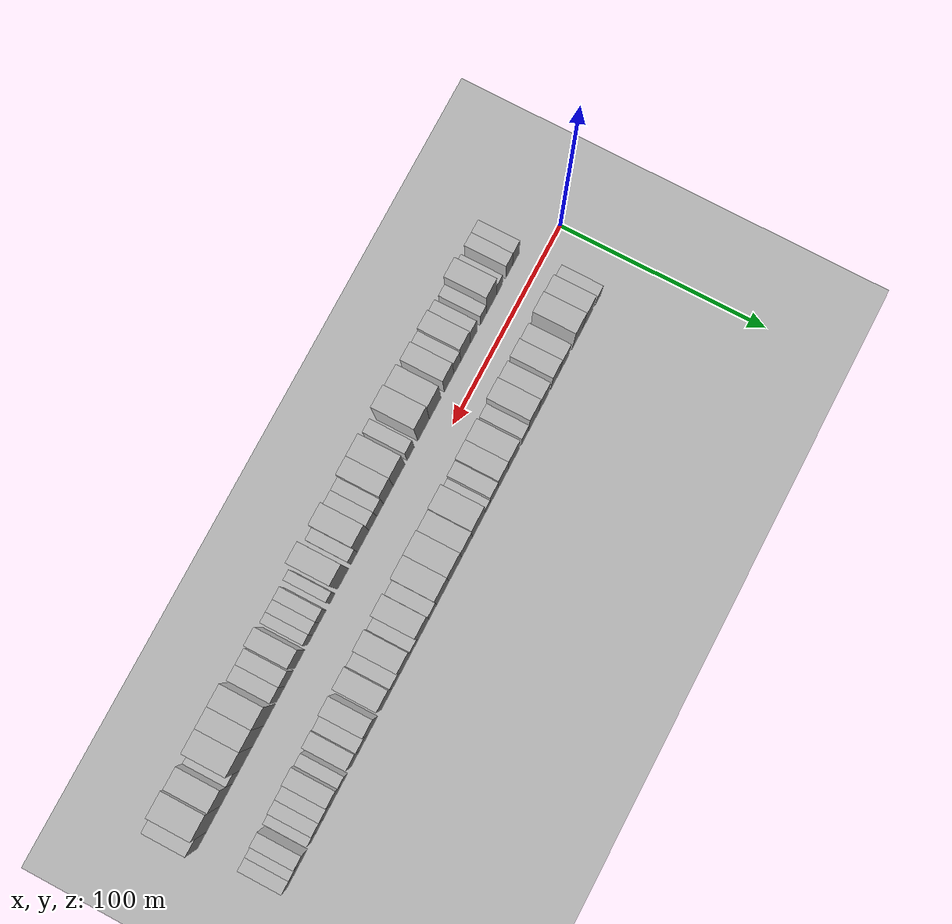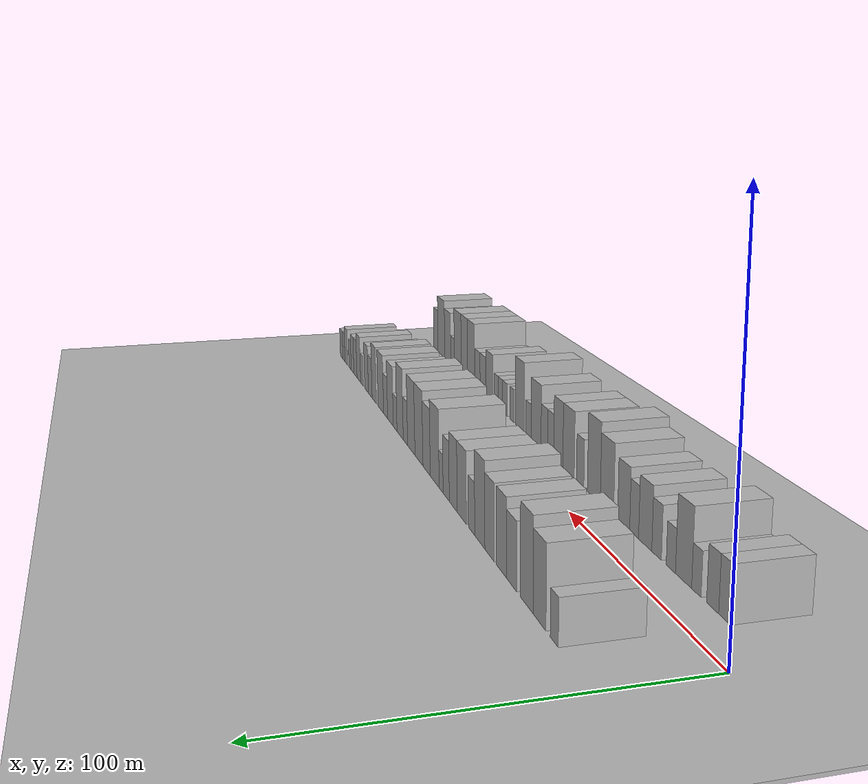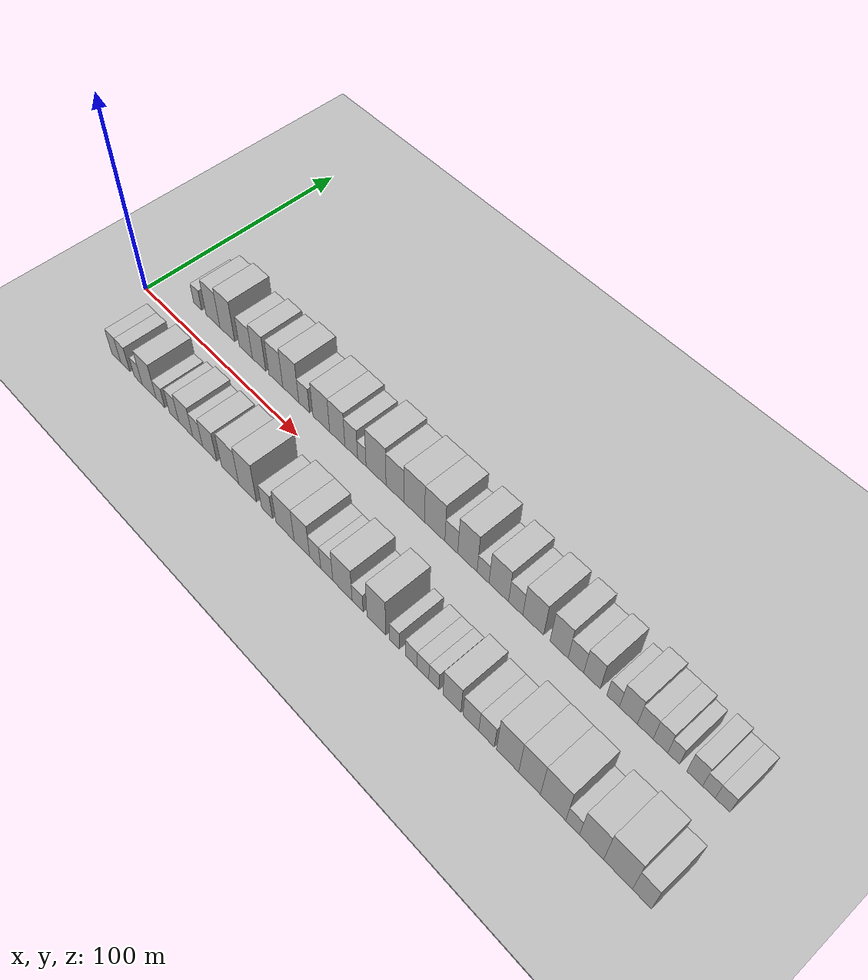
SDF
<?xml version="1.0" encoding="utf-8"?>

<sdf version="1.6">

   <world name="default">

      <gui fullscreen="0">

         <camera name="user_camera">

            <pose>-15 0 4.57585 0 0 0</pose>

            <view_controller>orbit</view_controller>

         </camera>

      </gui>

      <scene>

         <sky>

           <clouds>

             <speed>12</speed>

           </clouds>

         </sky>

         <ambient>0.4 0.4 0.4 1</ambient>

         <background>0.7 0.7 0.7 1</background>

         <shadows>1</shadows>

      </scene>

      <gravity>0 0 -9.8066</gravity>

      <magnetic_field>6e-06 2.3e-05 -4.2e-05</magnetic_field>

      <physics default="0" name="default_physics" type="ode">

         <ode>

            <solver>

               <type>quick</type>

               <iters>10</iters>

               <sor>1.0</sor>

               <use_dynamic_moi_rescaling>0</use_dynamic_moi_rescaling>

            </solver>

            <constraints>

               <cfm>0</cfm>

               <erp>0.2</erp>

               <contact_max_correcting_vel>100</contact_max_correcting_vel>

               <contact_surface_layer>0.001</contact_surface_layer>

            </constraints>

         </ode>

         <max_step_size>0.004</max_step_size>

         <real_time_factor>1</real_time_factor>

         <real_time_update_rate>250</real_time_update_rate>

      </physics>

      <light name="sun" type="directional">

         <cast_shadows>1</cast_shadows>

         <pose>0 0 10 0 0 0</pose>

         <diffuse>0.8 0.8 0.8 1</diffuse>

         <specular>0.2 0.2 0.2 1</specular>

         <attenuation>

            <range>1000</range>

            <constant>0.9</constant>

            <linear>0.01</linear>

            <quadratic>0.001</quadratic>

         </attenuation>

         <direction>-0.5 0.1 -0.9</direction>

      </light>

      <include>

         <name>ground_plane_1</name>

         <uri>model://HANNAS_ground_plane</uri>

         <pose>0 0 0  0 0 0</pose>

      </include>

      <include>

         <name>ground_plane_2</name>

         <uri>model://HANNAS_ground_plane</uri>

         <pose>100 0 0  0 0 0</pose>

      </include>

      <model name="building_1">

         <static>1</static>

         <pose frame="">22.7554 20.0000 0 0.000000 0.000000 1.570796</pose>

         <link name="link">

            <pose frame="">0 0 6.00 0 0 0</pose>

            <collision name="collision">

               <geometry>

                  <box>

                     <size>20.0000 5.5108 12.0000</size>

                  </box>

               </geometry>

               <max_contacts>10</max_contacts>

               <surface>

                  <contact>

                     <ode/>

                  </contact>

                  <bounce/>

                  <friction>

                     <torsional>

                        <ode/>

                     </torsional>

                     <ode/>

                  </friction>

               </surface>

            </collision>

            <visual name="visual">

               <cast_shadows>0</cast_shadows>

               <geometry>

                  <box>

                     <size>20.0000 5.5108 12.0000</size>

                  </box>

               </geometry>

               <material>

                  <script>

                     <uri>model://HANNAS_wall/materials/scripts</uri>

                     <uri>model://HANNAS_wall/materials/textures</uri>

                     <name>vrc/HANNAS_wall</name>

                  </script>

               </material>

            </visual>

            <self_collide>0</self_collide>

            <enable_wind>0</enable_wind>

            <kinematic>0</kinematic>

         </link>

      </model>

      <model name="building_2">

         <static>1</static>

         <pose frame="">33.1985 20.0000 0 0.000000 0.000000 1.570796</pose>

         <link name="link">

            <pose frame="">0 0 10.50 0 0 0</pose>

            <collision name="collision">

               <geometry>

                  <box>

                     <size>20.0000 9.3754 21.0000</size>

                  </box>

               </geometry>

               <max_contacts>10</max_contacts>

               <surface>

                  <contact>

                     <ode/>

                  </contact>

                  <bounce/>

                  <friction>

                     <torsional>

                        <ode/>

                     </torsional>

                     <ode/>

                  </friction>

               </surface>

            </collision>

            <visual name="visual">

               <cast_shadows>0</cast_shadows>

               <geometry>

                  <box>

                     <size>20.0000 9.3754 21.0000</size>

                  </box>

               </geometry>

               <material>

                  <script>

                     <uri>model://HANNAS_wall/materials/scripts</uri>

                     <uri>model://HANNAS_wall/materials/textures</uri>

                     <name>vrc/HANNAS_wall</name>

                  </script>

               </material>

            </visual>

            <self_collide>0</self_collide>

            <enable_wind>0</enable_wind>

            <kinematic>0</kinematic>

         </link>

      </model>

      <model name="building_3">

         <static>1</static>

         <pose frame="">42.8242 20.0000 0 0.000000 0.000000 1.570796</pose>

         <link name="link">

            <pose frame="">0 0 12.00 0 0 0</pose>

            <collision name="collision">

               <geometry>

                  <box>

                     <size>20.0000 9.8761 24.0000</size>

                  </box>

               </geometry>

               <max_contacts>10</max_contacts>

               <surface>

                  <contact>

                     <ode/>

                  </contact>

                  <bounce/>

                  <friction>

                     <torsional>

                        <ode/>

                     </torsional>

                     <ode/>

                  </friction>

               </surface>

            </collision>

            <visual name="visual">

               <cast_shadows>0</cast_shadows>

               <geometry>

                  <box>

                     <size>20.0000 9.8761 24.0000</size>

                  </box>

               </geometry>

               <material>

                  <script>

                     <uri>model://HANNAS_wall/materials/scripts</uri>

                     <uri>model://HANNAS_wall/materials/textures</uri>

                     <name>vrc/HANNAS_wall</name>

                  </script>

               </material>

            </visual>

            <self_collide>0</self_collide>

            <enable_wind>0</enable_wind>

            <kinematic>0</kinematic>

         </link>

      </model>

      <model name="building_4">

         <static>1</static>

         <pose frame="">55.0346 20.0000 0 0.000000 0.000000 1.570796</pose>

         <link name="link">

            <pose frame="">0 0 9.00 0 0 0</pose>

            <collision name="collision">

               <geometry>

                  <box>

                     <size>20.0000 8.5447 18.0000</size>

                  </box>

               </geometry>

               <max_contacts>10</max_contacts>

               <surface>

                  <contact>

                     <ode/>

                  </contact>

                  <bounce/>

                  <friction>

                     <torsional>

                        <ode/>

                     </torsional>

                     <ode/>

                  </friction>

               </surface>

            </collision>

            <visual name="visual">

               <cast_shadows>0</cast_shadows>

               <geometry>

                  <box>

                     <size>20.0000 8.5447 18.0000</size>

                  </box>

               </geometry>

               <material>

                  <script>

                     <uri>model://HANNAS_wall/materials/scripts</uri>

                     <uri>model://HANNAS_wall/materials/textures</uri>

                     <name>vrc/HANNAS_wall</name>

                  </script>

               </material>

            </visual>

            <self_collide>0</self_collide>

            <enable_wind>0</enable_wind>

            <kinematic>0</kinematic>

         </link>

      </model>

      <model name="building_5">

         <static>1</static>

         <pose frame="">63.5918 20.0000 0 0.000000 0.000000 1.570796</pose>

         <link name="link">

            <pose frame="">0 0 10.50 0 0 0</pose>

            <collision name="collision">

               <geometry>

                  <box>

                     <size>20.0000 8.5697 21.0000</size>

                  </box>

               </geometry>

               <max_contacts>10</max_contacts>

               <surface>

                  <contact>

                     <ode/>

                  </contact>

                  <bounce/>

                  <friction>

                     <torsional>

                        <ode/>

                     </torsional>

                     <ode/>

                  </friction>

               </surface>

            </collision>

            <visual name="visual">

               <cast_shadows>0</cast_shadows>

               <geometry>

                  <box>

                     <size>20.0000 8.5697 21.0000</size>

                  </box>

               </geometry>

               <material>

                  <script>

                     <uri>model://HANNAS_wall/materials/scripts</uri>

                     <uri>model://HANNAS_wall/materials/textures</uri>

                     <name>vrc/HANNAS_wall</name>

                  </script>

               </material>

            </visual>

            <self_collide>0</self_collide>

            <enable_wind>0</enable_wind>

            <kinematic>0</kinematic>

         </link>

      </model>

      <model name="building_6">

         <static>1</static>

         <pose frame="">74.2728 20.0000 0 0.000000 0.000000 1.570796</pose>

         <link name="link">

            <pose frame="">0 0 10.50 0 0 0</pose>

            <collision name="collision">

               <geometry>

                  <box>

                     <size>20.0000 8.7923 21.0000</size>

                  </box>

               </geometry>

               <max_contacts>10</max_contacts>

               <surface>

                  <contact>

                     <ode/>

                  </contact>

                  <bounce/>

                  <friction>

                     <torsional>

                        <ode/>

                     </torsional>

                     <ode/>

                  </friction>

               </surface>

            </collision>

            <visual name="visual">

               <cast_shadows>0</cast_shadows>

               <geometry>

                  <box>

                     <size>20.0000 8.7923 21.0000</size>

                  </box>

               </geometry>

               <material>

                  <script>

                     <uri>model://HANNAS_wall/materials/scripts</uri>

                     <uri>model://HANNAS_wall/materials/textures</uri>

                     <name>vrc/HANNAS_wall</name>

                  </script>

               </material>

            </visual>

            <self_collide>0</self_collide>

            <enable_wind>0</enable_wind>

            <kinematic>0</kinematic>

         </link>

      </model>

      <model name="building_7">

         <static>1</static>

         <pose frame="">83.6210 20.0000 0 0.000000 0.000000 1.570796</pose>

         <link name="link">

            <pose frame="">0 0 12.00 0 0 0</pose>

            <collision name="collision">

               <geometry>

                  <box>

                     <size>20.0000 9.9040 24.0000</size>

                  </box>

               </geometry>

               <max_contacts>10</max_contacts>

               <surface>

                  <contact>

                     <ode/>

                  </contact>

                  <bounce/>

                  <friction>

                     <torsional>

                        <ode/>

                     </torsional>

                     <ode/>

                  </friction>

               </surface>

            </collision>

            <visual name="visual">

               <cast_shadows>0</cast_shadows>

               <geometry>

                  <box>

                     <size>20.0000 9.9040 24.0000</size>

                  </box>

               </geometry>

               <material>

                  <script>

                     <uri>model://HANNAS_wall/materials/scripts</uri>

                     <uri>model://HANNAS_wall/materials/textures</uri>

                     <name>vrc/HANNAS_wall</name>

                  </script>

               </material>

            </visual>

            <self_collide>0</self_collide>

            <enable_wind>0</enable_wind>

            <kinematic>0</kinematic>

         </link>

      </model>

      <model name="building_8">

         <static>1</static>

         <pose frame="">91.8562 20.0000 0 0.000000 0.000000 1.570796</pose>

         <link name="link">

            <pose frame="">0 0 7.50 0 0 0</pose>

            <collision name="collision">

               <geometry>

                  <box>

                     <size>20.0000 6.5665 15.0000</size>

                  </box>

               </geometry>

               <max_contacts>10</max_contacts>

               <surface>

                  <contact>

                     <ode/>

                  </contact>

                  <bounce/>

                  <friction>

                     <torsional>

                        <ode/>

                     </torsional>

                     <ode/>

                  </friction>

               </surface>

            </collision>

            <visual name="visual">

               <cast_shadows>0</cast_shadows>

               <geometry>

                  <box>

                     <size>20.0000 6.5665 15.0000</size>

                  </box>

               </geometry>

               <material>

                  <script>

                     <uri>model://HANNAS_wall/materials/scripts</uri>

                     <uri>model://HANNAS_wall/materials/textures</uri>

                     <name>vrc/HANNAS_wall</name>

                  </script>

               </material>

            </visual>

            <self_collide>0</self_collide>

            <enable_wind>0</enable_wind>

            <kinematic>0</kinematic>

         </link>

      </model>

      <model name="building_9">

         <static>1</static>

         <pose frame="">102.1402 20.0000 0 0.000000 0.000000 1.570796</pose>

         <link name="link">

            <pose frame="">0 0 10.50 0 0 0</pose>

            <collision name="collision">

               <geometry>

                  <box>

                     <size>20.0000 10.0015 21.0000</size>

                  </box>

               </geometry>

               <max_contacts>10</max_contacts>

               <surface>

                  <contact>

                     <ode/>

                  </contact>

                  <bounce/>

                  <friction>

                     <torsional>

                        <ode/>

                     </torsional>

                     <ode/>

                  </friction>

               </surface>

            </collision>

            <visual name="visual">

               <cast_shadows>0</cast_shadows>

               <geometry>

                  <box>

                     <size>20.0000 10.0015 21.0000</size>

                  </box>

               </geometry>

               <material>

                  <script>

                     <uri>model://HANNAS_wall/materials/scripts</uri>

                     <uri>model://HANNAS_wall/materials/textures</uri>

                     <name>vrc/HANNAS_wall</name>

                  </script>

               </material>

            </visual>

            <self_collide>0</self_collide>

            <enable_wind>0</enable_wind>

            <kinematic>0</kinematic>

         </link>

      </model>

      <model name="building_10">

         <static>1</static>

         <pose frame="">111.6415 20.0000 0 0.000000 0.000000 1.570796</pose>

         <link name="link">

            <pose frame="">0 0 10.50 0 0 0</pose>

            <collision name="collision">

               <geometry>

                  <box>

                     <size>20.0000 9.0011 21.0000</size>

                  </box>

               </geometry>

               <max_contacts>10</max_contacts>

               <surface>

                  <contact>

                     <ode/>

                  </contact>

                  <bounce/>

                  <friction>

                     <torsional>

                        <ode/>

                     </torsional>

                     <ode/>

                  </friction>

               </surface>

            </collision>

            <visual name="visual">

               <cast_shadows>0</cast_shadows>

               <geometry>

                  <box>

                     <size>20.0000 9.0011 21.0000</size>

                  </box>

               </geometry>

               <material>

                  <script>

                     <uri>model://HANNAS_wall/materials/scripts</uri>

                     <uri>model://HANNAS_wall/materials/textures</uri>

                     <name>vrc/HANNAS_wall</name>

                  </script>

               </material>

            </visual>

            <self_collide>0</self_collide>

            <enable_wind>0</enable_wind>

            <kinematic>0</kinematic>

         </link>

      </model>

      <model name="building_11">

         <static>1</static>

         <pose frame="">119.8047 20.0000 0 0.000000 0.000000 1.570796</pose>

         <link name="link">

            <pose frame="">0 0 9.00 0 0 0</pose>

            <collision name="collision">

               <geometry>

                  <box>

                     <size>20.0000 7.3252 18.0000</size>

                  </box>

               </geometry>

               <max_contacts>10</max_contacts>

               <surface>

                  <contact>

                     <ode/>

                  </contact>

                  <bounce/>

                  <friction>

                     <torsional>

                        <ode/>

                     </torsional>

                     <ode/>

                  </friction>

               </surface>

            </collision>

            <visual name="visual">

               <cast_shadows>0</cast_shadows>

               <geometry>

                  <box>

                     <size>20.0000 7.3252 18.0000</size>

                  </box>

               </geometry>

               <material>

                  <script>

                     <uri>model://HANNAS_wall/materials/scripts</uri>

                     <uri>model://HANNAS_wall/materials/textures</uri>

                     <name>vrc/HANNAS_wall</name>

                  </script>

               </material>

            </visual>

            <self_collide>0</self_collide>

            <enable_wind>0</enable_wind>

            <kinematic>0</kinematic>

         </link>

      </model>

      <model name="building_12">

         <static>1</static>

         <pose frame="">125.8942 20.0000 0 0.000000 0.000000 1.570796</pose>

         <link name="link">

            <pose frame="">0 0 6.00 0 0 0</pose>

            <collision name="collision">

               <geometry>

                  <box>

                     <size>20.0000 4.8540 12.0000</size>

                  </box>

               </geometry>

               <max_contacts>10</max_contacts>

               <surface>

                  <contact>

                     <ode/>

                  </contact>

                  <bounce/>

                  <friction>

                     <torsional>

                        <ode/>

                     </torsional>

                     <ode/>

                  </friction>

               </surface>

            </collision>

            <visual name="visual">

               <cast_shadows>0</cast_shadows>

               <geometry>

                  <box>

                     <size>20.0000 4.8540 12.0000</size>

                  </box>

               </geometry>

               <material>

                  <script>

                     <uri>model://HANNAS_wall/materials/scripts</uri>

                     <uri>model://HANNAS_wall/materials/textures</uri>

                     <name>vrc/HANNAS_wall</name>

                  </script>

               </material>

            </visual>

            <self_collide>0</self_collide>

            <enable_wind>0</enable_wind>

            <kinematic>0</kinematic>

         </link>

      </model>

      <model name="building_13">

         <static>1</static>

         <pose frame="">133.9454 20.0000 0 0.000000 0.000000 1.570796</pose>

         <link name="link">

            <pose frame="">0 0 12.00 0 0 0</pose>

            <collision name="collision">

               <geometry>

                  <box>

                     <size>20.0000 11.2484 24.0000</size>

                  </box>

               </geometry>

               <max_contacts>10</max_contacts>

               <surface>

                  <contact>

                     <ode/>

                  </contact>

                  <bounce/>

                  <friction>

                     <torsional>

                        <ode/>

                     </torsional>

                     <ode/>

                  </friction>

               </surface>

            </collision>

            <visual name="visual">

               <cast_shadows>0</cast_shadows>

               <geometry>

                  <box>

                     <size>20.0000 11.2484 24.0000</size>

                  </box>

               </geometry>

               <material>

                  <script>

                     <uri>model://HANNAS_wall/materials/scripts</uri>

                     <uri>model://HANNAS_wall/materials/textures</uri>

                     <name>vrc/HANNAS_wall</name>

                  </script>

               </material>

            </visual>

            <self_collide>0</self_collide>

            <enable_wind>0</enable_wind>

            <kinematic>0</kinematic>

         </link>

      </model>

      <model name="building_14">

         <static>1</static>

         <pose frame="">144.4498 20.0000 0 0.000000 0.000000 1.570796</pose>

         <link name="link">

            <pose frame="">0 0 10.50 0 0 0</pose>

            <collision name="collision">

               <geometry>

                  <box>

                     <size>20.0000 9.7603 21.0000</size>

                  </box>

               </geometry>

               <max_contacts>10</max_contacts>

               <surface>

                  <contact>

                     <ode/>

                  </contact>

                  <bounce/>

                  <friction>

                     <torsional>

                        <ode/>

                     </torsional>

                     <ode/>

                  </friction>

               </surface>

            </collision>

            <visual name="visual">

               <cast_shadows>0</cast_shadows>

               <geometry>

                  <box>

                     <size>20.0000 9.7603 21.0000</size>

                  </box>

               </geometry>

               <material>

                  <script>

                     <uri>model://HANNAS_wall/materials/scripts</uri>

                     <uri>model://HANNAS_wall/materials/textures</uri>

                     <name>vrc/HANNAS_wall</name>

                  </script>

               </material>

            </visual>

            <self_collide>0</self_collide>

            <enable_wind>0</enable_wind>

            <kinematic>0</kinematic>

         </link>

      </model>

      <model name="building_15">

         <static>1</static>

         <pose frame="">154.9376 20.0000 0 0.000000 0.000000 1.570796</pose>

         <link name="link">

            <pose frame="">0 0 12.00 0 0 0</pose>

            <collision name="collision">

               <geometry>

                  <box>

                     <size>20.0000 11.2152 24.0000</size>

                  </box>

               </geometry>

               <max_contacts>10</max_contacts>

               <surface>

                  <contact>

                     <ode/>

                  </contact>

                  <bounce/>

                  <friction>

                     <torsional>

                        <ode/>

                     </torsional>

                     <ode/>

                  </friction>

               </surface>

            </collision>

            <visual name="visual">

               <cast_shadows>0</cast_shadows>

               <geometry>

                  <box>

                     <size>20.0000 11.2152 24.0000</size>

                  </box>

               </geometry>

               <material>

                  <script>

                     <uri>model://HANNAS_wall/materials/scripts</uri>

                     <uri>model://HANNAS_wall/materials/textures</uri>

                     <name>vrc/HANNAS_wall</name>

                  </script>

               </material>

            </visual>

            <self_collide>0</self_collide>

            <enable_wind>0</enable_wind>

            <kinematic>0</kinematic>

         </link>

      </model>

      <model name="building_16">

         <static>1</static>

         <pose frame="">165.9656 20.0000 0 0.000000 0.000000 1.570796</pose>

         <link name="link">

            <pose frame="">0 0 12.00 0 0 0</pose>

            <collision name="collision">

               <geometry>

                  <box>

                     <size>20.0000 10.8410 24.0000</size>

                  </box>

               </geometry>

               <max_contacts>10</max_contacts>

               <surface>

                  <contact>

                     <ode/>

                  </contact>

                  <bounce/>

                  <friction>

                     <torsional>

                        <ode/>

                     </torsional>

                     <ode/>

                  </friction>

               </surface>

            </collision>

            <visual name="visual">

               <cast_shadows>0</cast_shadows>

               <geometry>

                  <box>

                     <size>20.0000 10.8410 24.0000</size>

                  </box>

               </geometry>

               <material>

                  <script>

                     <uri>model://HANNAS_wall/materials/scripts</uri>

                     <uri>model://HANNAS_wall/materials/textures</uri>

                     <name>vrc/HANNAS_wall</name>

                  </script>

               </material>

            </visual>

            <self_collide>0</self_collide>

            <enable_wind>0</enable_wind>

            <kinematic>0</kinematic>

         </link>

      </model>

      <model name="building_17">

         <static>1</static>

         <pose frame="">174.7330 20.0000 0 0.000000 0.000000 1.570796</pose>

         <link name="link">

            <pose frame="">0 0 7.50 0 0 0</pose>

            <collision name="collision">

               <geometry>

                  <box>

                     <size>20.0000 6.6937 15.0000</size>

                  </box>

               </geometry>

               <max_contacts>10</max_contacts>

               <surface>

                  <contact>

                     <ode/>

                  </contact>

                  <bounce/>

                  <friction>

                     <torsional>

                        <ode/>

                     </torsional>

                     <ode/>

                  </friction>

               </surface>

            </collision>

            <visual name="visual">

               <cast_shadows>0</cast_shadows>

               <geometry>

                  <box>

                     <size>20.0000 6.6937 15.0000</size>

                  </box>

               </geometry>

               <material>

                  <script>

                     <uri>model://HANNAS_wall/materials/scripts</uri>

                     <uri>model://HANNAS_wall/materials/textures</uri>

                     <name>vrc/HANNAS_wall</name>

                  </script>

               </material>

            </visual>

            <self_collide>0</self_collide>

            <enable_wind>0</enable_wind>

            <kinematic>0</kinematic>

         </link>

      </model>

      <model name="building_18">

         <static>1</static>

         <pose frame="">183.0394 20.0000 0 0.000000 0.000000 1.570796</pose>

         <link name="link">

            <pose frame="">0 0 12.00 0 0 0</pose>

            <collision name="collision">

               <geometry>

                  <box>

                     <size>20.0000 9.9190 24.0000</size>

                  </box>

               </geometry>

               <max_contacts>10</max_contacts>

               <surface>

                  <contact>

                     <ode/>

                  </contact>

                  <bounce/>

                  <friction>

                     <torsional>

                        <ode/>

                     </torsional>

                     <ode/>

                  </friction>

               </surface>

            </collision>

            <visual name="visual">

               <cast_shadows>0</cast_shadows>

               <geometry>

                  <box>

                     <size>20.0000 9.9190 24.0000</size>

                  </box>

               </geometry>

               <material>

                  <script>

                     <uri>model://HANNAS_wall/materials/scripts</uri>

                     <uri>model://HANNAS_wall/materials/textures</uri>

                     <name>vrc/HANNAS_wall</name>

                  </script>

               </material>

            </visual>

            <self_collide>0</self_collide>

            <enable_wind>0</enable_wind>

            <kinematic>0</kinematic>

         </link>

      </model>

      <model name="building_19">

         <static>1</static>

         <pose frame="">190.9892 20.0000 0 0.000000 0.000000 1.570796</pose>

         <link name="link">

            <pose frame="">0 0 6.00 0 0 0</pose>

            <collision name="collision">

               <geometry>

                  <box>

                     <size>20.0000 5.9807 12.0000</size>

                  </box>

               </geometry>

               <max_contacts>10</max_contacts>

               <surface>

                  <contact>

                     <ode/>

                  </contact>

                  <bounce/>

                  <friction>

                     <torsional>

                        <ode/>

                     </torsional>

                     <ode/>

                  </friction>

               </surface>

            </collision>

            <visual name="visual">

               <cast_shadows>0</cast_shadows>

               <geometry>

                  <box>

                     <size>20.0000 5.9807 12.0000</size>

                  </box>

               </geometry>

               <material>

                  <script>

                     <uri>model://HANNAS_wall/materials/scripts</uri>

                     <uri>model://HANNAS_wall/materials/textures</uri>

                     <name>vrc/HANNAS_wall</name>

                  </script>

               </material>

            </visual>

            <self_collide>0</self_collide>

            <enable_wind>0</enable_wind>

            <kinematic>0</kinematic>

         </link>

      </model>

      <model name="building_20">

         <static>1</static>

         <pose frame="">198.8270 20.0000 0 0.000000 0.000000 1.570796</pose>

         <link name="link">

            <pose frame="">0 0 10.50 0 0 0</pose>

            <collision name="collision">

               <geometry>

                  <box>

                     <size>20.0000 9.6948 21.0000</size>

                  </box>

               </geometry>

               <max_contacts>10</max_contacts>

               <surface>

                  <contact>

                     <ode/>

                  </contact>

                  <bounce/>

                  <friction>

                     <torsional>

                        <ode/>

                     </torsional>

                     <ode/>

                  </friction>

               </surface>

            </collision>

            <visual name="visual">

               <cast_shadows>0</cast_shadows>

               <geometry>

                  <box>

                     <size>20.0000 9.6948 21.0000</size>

                  </box>

               </geometry>

               <material>

                  <script>

                     <uri>model://HANNAS_wall/materials/scripts</uri>

                     <uri>model://HANNAS_wall/materials/textures</uri>

                     <name>vrc/HANNAS_wall</name>

                  </script>

               </material>

            </visual>

            <self_collide>0</self_collide>

            <enable_wind>0</enable_wind>

            <kinematic>0</kinematic>

         </link>

      </model>

      <model name="building_21">

         <static>1</static>

         <pose frame="">207.1692 20.0000 0 0.000000 0.000000 1.570796</pose>

         <link name="link">

            <pose frame="">0 0 7.50 0 0 0</pose>

            <collision name="collision">

               <geometry>

                  <box>

                     <size>20.0000 6.9896 15.0000</size>

                  </box>

               </geometry>

               <max_contacts>10</max_contacts>

               <surface>

                  <contact>

                     <ode/>

                  </contact>

                  <bounce/>

                  <friction>

                     <torsional>

                        <ode/>

                     </torsional>

                     <ode/>

                  </friction>

               </surface>

            </collision>

            <visual name="visual">

               <cast_shadows>0</cast_shadows>

               <geometry>

                  <box>

                     <size>20.0000 6.9896 15.0000</size>

                  </box>

               </geometry>

               <material>

                  <script>

                     <uri>model://HANNAS_wall/materials/scripts</uri>

                     <uri>model://HANNAS_wall/materials/textures</uri>

                     <name>vrc/HANNAS_wall</name>

                  </script>

               </material>

            </visual>

            <self_collide>0</self_collide>

            <enable_wind>0</enable_wind>

            <kinematic>0</kinematic>

         </link>

      </model>

      <model name="building_22">

         <static>1</static>

         <pose frame="">215.6674 20.0000 0 0.000000 0.000000 1.570796</pose>

         <link name="link">

            <pose frame="">0 0 10.50 0 0 0</pose>

            <collision name="collision">

               <geometry>

                  <box>

                     <size>20.0000 10.0068 21.0000</size>

                  </box>

               </geometry>

               <max_contacts>10</max_contacts>

               <surface>

                  <contact>

                     <ode/>

                  </contact>

                  <bounce/>

                  <friction>

                     <torsional>

                        <ode/>

                     </torsional>

                     <ode/>

                  </friction>

               </surface>

            </collision>

            <visual name="visual">

               <cast_shadows>0</cast_shadows>

               <geometry>

                  <box>

                     <size>20.0000 10.0068 21.0000</size>

                  </box>

               </geometry>

               <material>

                  <script>

                     <uri>model://HANNAS_wall/materials/scripts</uri>

                     <uri>model://HANNAS_wall/materials/textures</uri>

                     <name>vrc/HANNAS_wall</name>

                  </script>

               </material>

            </visual>

            <self_collide>0</self_collide>

            <enable_wind>0</enable_wind>

            <kinematic>0</kinematic>

         </link>

      </model>

      <model name="building_23">

         <static>1</static>

         <pose frame="">227.8896 20.0000 0 0.000000 0.000000 1.570796</pose>

         <link name="link">

            <pose frame="">0 0 10.50 0 0 0</pose>

            <collision name="collision">

               <geometry>

                  <box>

                     <size>20.0000 8.4376 21.0000</size>

                  </box>

               </geometry>

               <max_contacts>10</max_contacts>

               <surface>

                  <contact>

                     <ode/>

                  </contact>

                  <bounce/>

                  <friction>

                     <torsional>

                        <ode/>

                     </torsional>

                     <ode/>

                  </friction>

               </surface>

            </collision>

            <visual name="visual">

               <cast_shadows>0</cast_shadows>

               <geometry>

                  <box>

                     <size>20.0000 8.4376 21.0000</size>

                  </box>

               </geometry>

               <material>

                  <script>

                     <uri>model://HANNAS_wall/materials/scripts</uri>

                     <uri>model://HANNAS_wall/materials/textures</uri>

                     <name>vrc/HANNAS_wall</name>

                  </script>

               </material>

            </visual>

            <self_collide>0</self_collide>

            <enable_wind>0</enable_wind>

            <kinematic>0</kinematic>

         </link>

      </model>

      <model name="building_24">

         <static>1</static>

         <pose frame="">235.6966 20.0000 0 0.000000 0.000000 1.570796</pose>

         <link name="link">

            <pose frame="">0 0 7.50 0 0 0</pose>

            <collision name="collision">

               <geometry>

                  <box>

                     <size>20.0000 7.1764 15.0000</size>

                  </box>

               </geometry>

               <max_contacts>10</max_contacts>

               <surface>

                  <contact>

                     <ode/>

                  </contact>

                  <bounce/>

                  <friction>

                     <torsional>

                        <ode/>

                     </torsional>

                     <ode/>

                  </friction>

               </surface>

            </collision>

            <visual name="visual">

               <cast_shadows>0</cast_shadows>

               <geometry>

                  <box>

                     <size>20.0000 7.1764 15.0000</size>

                  </box>

               </geometry>

               <material>

                  <script>

                     <uri>model://HANNAS_wall/materials/scripts</uri>

                     <uri>model://HANNAS_wall/materials/textures</uri>

                     <name>vrc/HANNAS_wall</name>

                  </script>

               </material>

            </visual>

            <self_collide>0</self_collide>

            <enable_wind>0</enable_wind>

            <kinematic>0</kinematic>

         </link>

      </model>

      <model name="building_25">

         <static>1</static>

         <pose frame="">243.0380 20.0000 0 0.000000 0.000000 1.570796</pose>

         <link name="link">

            <pose frame="">0 0 9.00 0 0 0</pose>

            <collision name="collision">

               <geometry>

                  <box>

                     <size>20.0000 7.5064 18.0000</size>

                  </box>

               </geometry>

               <max_contacts>10</max_contacts>

               <surface>

                  <contact>

                     <ode/>

                  </contact>

                  <bounce/>

                  <friction>

                     <torsional>

                        <ode/>

                     </torsional>

                     <ode/>

                  </friction>

               </surface>

            </collision>

            <visual name="visual">

               <cast_shadows>0</cast_shadows>

               <geometry>

                  <box>

                     <size>20.0000 7.5064 18.0000</size>

                  </box>

               </geometry>

               <material>

                  <script>

                     <uri>model://HANNAS_wall/materials/scripts</uri>

                     <uri>model://HANNAS_wall/materials/textures</uri>

                     <name>vrc/HANNAS_wall</name>

                  </script>

               </material>

            </visual>

            <self_collide>0</self_collide>

            <enable_wind>0</enable_wind>

            <kinematic>0</kinematic>

         </link>

      </model>

      <model name="building_26">

         <static>1</static>

         <pose frame="">252.5489 20.0000 0 0.000000 0.000000 1.570796</pose>

         <link name="link">

            <pose frame="">0 0 6.00 0 0 0</pose>

            <collision name="collision">

               <geometry>

                  <box>

                     <size>20.0000 5.5153 12.0000</size>

                  </box>

               </geometry>

               <max_contacts>10</max_contacts>

               <surface>

                  <contact>

                     <ode/>

                  </contact>

                  <bounce/>

                  <friction>

                     <torsional>

                        <ode/>

                     </torsional>

                     <ode/>

                  </friction>

               </surface>

            </collision>

            <visual name="visual">

               <cast_shadows>0</cast_shadows>

               <geometry>

                  <box>

                     <size>20.0000 5.5153 12.0000</size>

                  </box>

               </geometry>

               <material>

                  <script>

                     <uri>model://HANNAS_wall/materials/scripts</uri>

                     <uri>model://HANNAS_wall/materials/textures</uri>

                     <name>vrc/HANNAS_wall</name>

                  </script>

               </material>

            </visual>

            <self_collide>0</self_collide>

            <enable_wind>0</enable_wind>

            <kinematic>0</kinematic>

         </link>

      </model>

      <model name="building_27">

         <static>1</static>

         <pose frame="">259.2600 20.0000 0 0.000000 0.000000 1.570796</pose>

         <link name="link">

            <pose frame="">0 0 9.00 0 0 0</pose>

            <collision name="collision">

               <geometry>

                  <box>

                     <size>20.0000 7.9069 18.0000</size>

                  </box>

               </geometry>

               <max_contacts>10</max_contacts>

               <surface>

                  <contact>

                     <ode/>

                  </contact>

                  <bounce/>

                  <friction>

                     <torsional>

                        <ode/>

                     </torsional>

                     <ode/>

                  </friction>

               </surface>

            </collision>

            <visual name="visual">

               <cast_shadows>0</cast_shadows>

               <geometry>

                  <box>

                     <size>20.0000 7.9069 18.0000</size>

                  </box>

               </geometry>

               <material>

                  <script>

                     <uri>model://HANNAS_wall/materials/scripts</uri>

                     <uri>model://HANNAS_wall/materials/textures</uri>

                     <name>vrc/HANNAS_wall</name>

                  </script>

               </material>

            </visual>

            <self_collide>0</self_collide>

            <enable_wind>0</enable_wind>

            <kinematic>0</kinematic>

         </link>

      </model>

      <model name="building_28">

         <static>1</static>

         <pose frame="">266.5928 20.0000 0 0.000000 0.000000 1.570796</pose>

         <link name="link">

            <pose frame="">0 0 7.50 0 0 0</pose>

            <collision name="collision">

               <geometry>

                  <box>

                     <size>20.0000 6.7587 15.0000</size>

                  </box>

               </geometry>

               <max_contacts>10</max_contacts>

               <surface>

                  <contact>

                     <ode/>

                  </contact>

                  <bounce/>

                  <friction>

                     <torsional>

                        <ode/>

                     </torsional>

                     <ode/>

                  </friction>

               </surface>

            </collision>

            <visual name="visual">

               <cast_shadows>0</cast_shadows>

               <geometry>

                  <box>

                     <size>20.0000 6.7587 15.0000</size>

                  </box>

               </geometry>

               <material>

                  <script>

                     <uri>model://HANNAS_wall/materials/scripts</uri>

                     <uri>model://HANNAS_wall/materials/textures</uri>

                     <name>vrc/HANNAS_wall</name>

                  </script>

               </material>

            </visual>

            <self_collide>0</self_collide>

            <enable_wind>0</enable_wind>

            <kinematic>0</kinematic>

         </link>

      </model>

      <model name="building_29">

         <static>1</static>

         <pose frame="">273.0589 20.0000 0 0.000000 0.000000 1.570796</pose>

         <link name="link">

            <pose frame="">0 0 7.50 0 0 0</pose>

            <collision name="collision">

               <geometry>

                  <box>

                     <size>20.0000 6.1735 15.0000</size>

                  </box>

               </geometry>

               <max_contacts>10</max_contacts>

               <surface>

                  <contact>

                     <ode/>

                  </contact>

                  <bounce/>

                  <friction>

                     <torsional>

                        <ode/>

                     </torsional>

                     <ode/>

                  </friction>

               </surface>

            </collision>

            <visual name="visual">

               <cast_shadows>0</cast_shadows>

               <geometry>

                  <box>

                     <size>20.0000 6.1735 15.0000</size>

                  </box>

               </geometry>

               <material>

                  <script>

                     <uri>model://HANNAS_wall/materials/scripts</uri>

                     <uri>model://HANNAS_wall/materials/textures</uri>

                     <name>vrc/HANNAS_wall</name>

                  </script>

               </material>

            </visual>

            <self_collide>0</self_collide>

            <enable_wind>0</enable_wind>

            <kinematic>0</kinematic>

         </link>

      </model>

      <model name="building_30">

         <static>1</static>

         <pose frame="">278.6506 20.0000 0 0.000000 0.000000 1.570796</pose>

         <link name="link">

            <pose frame="">0 0 6.00 0 0 0</pose>

            <collision name="collision">

               <geometry>

                  <box>

                     <size>20.0000 5.0098 12.0000</size>

                  </box>

               </geometry>

               <max_contacts>10</max_contacts>

               <surface>

                  <contact>

                     <ode/>

                  </contact>

                  <bounce/>

                  <friction>

                     <torsional>

                        <ode/>

                     </torsional>

                     <ode/>

                  </friction>

               </surface>

            </collision>

            <visual name="visual">

               <cast_shadows>0</cast_shadows>

               <geometry>

                  <box>

                     <size>20.0000 5.0098 12.0000</size>

                  </box>

               </geometry>

               <material>

                  <script>

                     <uri>model://HANNAS_wall/materials/scripts</uri>

                     <uri>model://HANNAS_wall/materials/textures</uri>

                     <name>vrc/HANNAS_wall</name>

                  </script>

               </material>

            </visual>

            <self_collide>0</self_collide>

            <enable_wind>0</enable_wind>

            <kinematic>0</kinematic>

         </link>

      </model>

      <model name="building_31">

         <static>1</static>

         <pose frame="">287.4154 20.0000 0 0.000000 0.000000 1.570796</pose>

         <link name="link">

            <pose frame="">0 0 7.50 0 0 0</pose>

            <collision name="collision">

               <geometry>

                  <box>

                     <size>20.0000 6.5198 15.0000</size>

                  </box>

               </geometry>

               <max_contacts>10</max_contacts>

               <surface>

                  <contact>

                     <ode/>

                  </contact>

                  <bounce/>

                  <friction>

                     <torsional>

                        <ode/>

                     </torsional>

                     <ode/>

                  </friction>

               </surface>

            </collision>

            <visual name="visual">

               <cast_shadows>0</cast_shadows>

               <geometry>

                  <box>

                     <size>20.0000 6.5198 15.0000</size>

                  </box>

               </geometry>

               <material>

                  <script>

                     <uri>model://HANNAS_wall/materials/scripts</uri>

                     <uri>model://HANNAS_wall/materials/textures</uri>

                     <name>vrc/HANNAS_wall</name>

                  </script>

               </material>

            </visual>

            <self_collide>0</self_collide>

            <enable_wind>0</enable_wind>

            <kinematic>0</kinematic>

         </link>

      </model>

      <model name="building_32">

         <static>1</static>

         <pose frame="">293.2483 20.0000 0 0.000000 0.000000 1.570796</pose>

         <link name="link">

            <pose frame="">0 0 6.00 0 0 0</pose>

            <collision name="collision">

               <geometry>

                  <box>

                     <size>20.0000 5.1459 12.0000</size>

                  </box>

               </geometry>

               <max_contacts>10</max_contacts>

               <surface>

                  <contact>

                     <ode/>

                  </contact>

                  <bounce/>

                  <friction>

                     <torsional>

                        <ode/>

                     </torsional>

                     <ode/>

                  </friction>

               </surface>

            </collision>

            <visual name="visual">

               <cast_shadows>0</cast_shadows>

               <geometry>

                  <box>

                     <size>20.0000 5.1459 12.0000</size>

                  </box>

               </geometry>

               <material>

                  <script>

                     <uri>model://HANNAS_wall/materials/scripts</uri>

                     <uri>model://HANNAS_wall/materials/textures</uri>

                     <name>vrc/HANNAS_wall</name>

                  </script>

               </material>

            </visual>

            <self_collide>0</self_collide>

            <enable_wind>0</enable_wind>

            <kinematic>0</kinematic>

         </link>

      </model>

      <model name="building_33">

         <static>1</static>

         <pose frame="">298.8159 20.0000 0 0.000000 0.000000 1.570796</pose>

         <link name="link">

            <pose frame="">0 0 6.00 0 0 0</pose>

            <collision name="collision">

               <geometry>

                  <box>

                     <size>20.0000 5.9893 12.0000</size>

                  </box>

               </geometry>

               <max_contacts>10</max_contacts>

               <surface>

                  <contact>

                     <ode/>

                  </contact>

                  <bounce/>

                  <friction>

                     <torsional>

                        <ode/>

                     </torsional>

                     <ode/>

                  </friction>

               </surface>

            </collision>

            <visual name="visual">

               <cast_shadows>0</cast_shadows>

               <geometry>

                  <box>

                     <size>20.0000 5.9893 12.0000</size>

                  </box>

               </geometry>

               <material>

                  <script>

                     <uri>model://HANNAS_wall/materials/scripts</uri>

                     <uri>model://HANNAS_wall/materials/textures</uri>

                     <name>vrc/HANNAS_wall</name>

                  </script>

               </material>

            </visual>

            <self_collide>0</self_collide>

            <enable_wind>0</enable_wind>

            <kinematic>0</kinematic>

         </link>

      </model>

      <model name="building_34">

         <static>1</static>

         <pose frame="">23.1378 -20.0000 0 0.000000 0.000000 1.570796</pose>

         <link name="link">

            <pose frame="">0 0 7.50 0 0 0</pose>

            <collision name="collision">

               <geometry>

                  <box>

                     <size>20.0000 6.2755 15.0000</size>

                  </box>

               </geometry>

               <max_contacts>10</max_contacts>

               <surface>

                  <contact>

                     <ode/>

                  </contact>

                  <bounce/>

                  <friction>

                     <torsional>

                        <ode/>

                     </torsional>

                     <ode/>

                  </friction>

               </surface>

            </collision>

            <visual name="visual">

               <cast_shadows>0</cast_shadows>

               <geometry>

                  <box>

                     <size>20.0000 6.2755 15.0000</size>

                  </box>

               </geometry>

               <material>

                  <script>

                     <uri>model://HANNAS_wall/materials/scripts</uri>

                     <uri>model://HANNAS_wall/materials/textures</uri>

                     <name>vrc/HANNAS_wall</name>

                  </script>

               </material>

            </visual>

            <self_collide>0</self_collide>

            <enable_wind>0</enable_wind>

            <kinematic>0</kinematic>

         </link>

      </model>

      <model name="building_35">

         <static>1</static>

         <pose frame="">29.5007 -20.0000 0 0.000000 0.000000 1.570796</pose>

         <link name="link">

            <pose frame="">0 0 7.50 0 0 0</pose>

            <collision name="collision">

               <geometry>

                  <box>

                     <size>20.0000 6.4504 15.0000</size>

                  </box>

               </geometry>

               <max_contacts>10</max_contacts>

               <surface>

                  <contact>

                     <ode/>

                  </contact>

                  <bounce/>

                  <friction>

                     <torsional>

                        <ode/>

                     </torsional>

                     <ode/>

                  </friction>

               </surface>

            </collision>

            <visual name="visual">

               <cast_shadows>0</cast_shadows>

               <geometry>

                  <box>

                     <size>20.0000 6.4504 15.0000</size>

                  </box>

               </geometry>

               <material>

                  <script>

                     <uri>model://HANNAS_wall/materials/scripts</uri>

                     <uri>model://HANNAS_wall/materials/textures</uri>

                     <name>vrc/HANNAS_wall</name>

                  </script>

               </material>

            </visual>

            <self_collide>0</self_collide>

            <enable_wind>0</enable_wind>

            <kinematic>0</kinematic>

         </link>

      </model>

      <model name="building_36">

         <static>1</static>

         <pose frame="">38.4031 -20.0000 0 0.000000 0.000000 1.570796</pose>

         <link name="link">

            <pose frame="">0 0 6.00 0 0 0</pose>

            <collision name="collision">

               <geometry>

                  <box>

                     <size>20.0000 5.3543 12.0000</size>

                  </box>

               </geometry>

               <max_contacts>10</max_contacts>

               <surface>

                  <contact>

                     <ode/>

                  </contact>

                  <bounce/>

                  <friction>

                     <torsional>

                        <ode/>

                     </torsional>

                     <ode/>

                  </friction>

               </surface>

            </collision>

            <visual name="visual">

               <cast_shadows>0</cast_shadows>

               <geometry>

                  <box>

                     <size>20.0000 5.3543 12.0000</size>

                  </box>

               </geometry>

               <material>

                  <script>

                     <uri>model://HANNAS_wall/materials/scripts</uri>

                     <uri>model://HANNAS_wall/materials/textures</uri>

                     <name>vrc/HANNAS_wall</name>

                  </script>

               </material>

            </visual>

            <self_collide>0</self_collide>

            <enable_wind>0</enable_wind>

            <kinematic>0</kinematic>

         </link>

      </model>

      <model name="building_37">

         <static>1</static>

         <pose frame="">45.8455 -20.0000 0 0.000000 0.000000 1.570796</pose>

         <link name="link">

            <pose frame="">0 0 10.50 0 0 0</pose>

            <collision name="collision">

               <geometry>

                  <box>

                     <size>20.0000 9.5305 21.0000</size>

                  </box>

               </geometry>

               <max_contacts>10</max_contacts>

               <surface>

                  <contact>

                     <ode/>

                  </contact>

                  <bounce/>

                  <friction>

                     <torsional>

                        <ode/>

                     </torsional>

                     <ode/>

                  </friction>

               </surface>

            </collision>

            <visual name="visual">

               <cast_shadows>0</cast_shadows>

               <geometry>

                  <box>

                     <size>20.0000 9.5305 21.0000</size>

                  </box>

               </geometry>

               <material>

                  <script>

                     <uri>model://HANNAS_wall/materials/scripts</uri>

                     <uri>model://HANNAS_wall/materials/textures</uri>

                     <name>vrc/HANNAS_wall</name>

                  </script>

               </material>

            </visual>

            <self_collide>0</self_collide>

            <enable_wind>0</enable_wind>

            <kinematic>0</kinematic>

         </link>

      </model>

      <model name="building_38">

         <static>1</static>

         <pose frame="">53.4544 -20.0000 0 0.000000 0.000000 1.570796</pose>

         <link name="link">

            <pose frame="">0 0 6.00 0 0 0</pose>

            <collision name="collision">

               <geometry>

                  <box>

                     <size>20.0000 5.6874 12.0000</size>

                  </box>

               </geometry>

               <max_contacts>10</max_contacts>

               <surface>

                  <contact>

                     <ode/>

                  </contact>

                  <bounce/>

                  <friction>

                     <torsional>

                        <ode/>

                     </torsional>

                     <ode/>

                  </friction>

               </surface>

            </collision>

            <visual name="visual">

               <cast_shadows>0</cast_shadows>

               <geometry>

                  <box>

                     <size>20.0000 5.6874 12.0000</size>

                  </box>

               </geometry>

               <material>

                  <script>

                     <uri>model://HANNAS_wall/materials/scripts</uri>

                     <uri>model://HANNAS_wall/materials/textures</uri>

                     <name>vrc/HANNAS_wall</name>

                  </script>

               </material>

            </visual>

            <self_collide>0</self_collide>

            <enable_wind>0</enable_wind>

            <kinematic>0</kinematic>

         </link>

      </model>

      <model name="building_39">

         <static>1</static>

         <pose frame="">62.4285 -20.0000 0 0.000000 0.000000 1.570796</pose>

         <link name="link">

            <pose frame="">0 0 7.50 0 0 0</pose>

            <collision name="collision">

               <geometry>

                  <box>

                     <size>20.0000 6.2608 15.0000</size>

                  </box>

               </geometry>

               <max_contacts>10</max_contacts>

               <surface>

                  <contact>

                     <ode/>

                  </contact>

                  <bounce/>

                  <friction>

                     <torsional>

                        <ode/>

                     </torsional>

                     <ode/>

                  </friction>

               </surface>

            </collision>

            <visual name="visual">

               <cast_shadows>0</cast_shadows>

               <geometry>

                  <box>

                     <size>20.0000 6.2608 15.0000</size>

                  </box>

               </geometry>

               <material>

                  <script>

                     <uri>model://HANNAS_wall/materials/scripts</uri>

                     <uri>model://HANNAS_wall/materials/textures</uri>

                     <name>vrc/HANNAS_wall</name>

                  </script>

               </material>

            </visual>

            <self_collide>0</self_collide>

            <enable_wind>0</enable_wind>

            <kinematic>0</kinematic>

         </link>

      </model>

      <model name="building_40">

         <static>1</static>

         <pose frame="">70.0182 -20.0000 0 0.000000 0.000000 1.570796</pose>

         <link name="link">

            <pose frame="">0 0 9.00 0 0 0</pose>

            <collision name="collision">

               <geometry>

                  <box>

                     <size>20.0000 8.9185 18.0000</size>

                  </box>

               </geometry>

               <max_contacts>10</max_contacts>

               <surface>

                  <contact>

                     <ode/>

                  </contact>

                  <bounce/>

                  <friction>

                     <torsional>

                        <ode/>

                     </torsional>

                     <ode/>

                  </friction>

               </surface>

            </collision>

            <visual name="visual">

               <cast_shadows>0</cast_shadows>

               <geometry>

                  <box>

                     <size>20.0000 8.9185 18.0000</size>

                  </box>

               </geometry>

               <material>

                  <script>

                     <uri>model://HANNAS_wall/materials/scripts</uri>

                     <uri>model://HANNAS_wall/materials/textures</uri>

                     <name>vrc/HANNAS_wall</name>

                  </script>

               </material>

            </visual>

            <self_collide>0</self_collide>

            <enable_wind>0</enable_wind>

            <kinematic>0</kinematic>

         </link>

      </model>

      <model name="building_41">

         <static>1</static>

         <pose frame="">77.6139 -20.0000 0 0.000000 0.000000 1.570796</pose>

         <link name="link">

            <pose frame="">0 0 7.50 0 0 0</pose>

            <collision name="collision">

               <geometry>

                  <box>

                     <size>20.0000 6.2729 15.0000</size>

                  </box>

               </geometry>

               <max_contacts>10</max_contacts>

               <surface>

                  <contact>

                     <ode/>

                  </contact>

                  <bounce/>

                  <friction>

                     <torsional>

                        <ode/>

                     </torsional>

                     <ode/>

                  </friction>

               </surface>

            </collision>

            <visual name="visual">

               <cast_shadows>0</cast_shadows>

               <geometry>

                  <box>

                     <size>20.0000 6.2729 15.0000</size>

                  </box>

               </geometry>

               <material>

                  <script>

                     <uri>model://HANNAS_wall/materials/scripts</uri>

                     <uri>model://HANNAS_wall/materials/textures</uri>

                     <name>vrc/HANNAS_wall</name>

                  </script>

               </material>

            </visual>

            <self_collide>0</self_collide>

            <enable_wind>0</enable_wind>

            <kinematic>0</kinematic>

         </link>

      </model>

      <model name="building_42">

         <static>1</static>

         <pose frame="">85.1703 -20.0000 0 0.000000 0.000000 1.570796</pose>

         <link name="link">

            <pose frame="">0 0 9.00 0 0 0</pose>

            <collision name="collision">

               <geometry>

                  <box>

                     <size>20.0000 8.8398 18.0000</size>

                  </box>

               </geometry>

               <max_contacts>10</max_contacts>

               <surface>

                  <contact>

                     <ode/>

                  </contact>

                  <bounce/>

                  <friction>

                     <torsional>

                        <ode/>

                     </torsional>

                     <ode/>

                  </friction>

               </surface>

            </collision>

            <visual name="visual">

               <cast_shadows>0</cast_shadows>

               <geometry>

                  <box>

                     <size>20.0000 8.8398 18.0000</size>

                  </box>

               </geometry>

               <material>

                  <script>

                     <uri>model://HANNAS_wall/materials/scripts</uri>

                     <uri>model://HANNAS_wall/materials/textures</uri>

                     <name>vrc/HANNAS_wall</name>

                  </script>

               </material>

            </visual>

            <self_collide>0</self_collide>

            <enable_wind>0</enable_wind>

            <kinematic>0</kinematic>

         </link>

      </model>

      <model name="building_43">

         <static>1</static>

         <pose frame="">97.8360 -20.0000 0 0.000000 0.000000 1.570796</pose>

         <link name="link">

            <pose frame="">0 0 10.50 0 0 0</pose>

            <collision name="collision">

               <geometry>

                  <box>

                     <size>20.0000 10.4916 21.0000</size>

                  </box>

               </geometry>

               <max_contacts>10</max_contacts>

               <surface>

                  <contact>

                     <ode/>

                  </contact>

                  <bounce/>

                  <friction>

                     <torsional>

                        <ode/>

                     </torsional>

                     <ode/>

                  </friction>

               </surface>

            </collision>

            <visual name="visual">

               <cast_shadows>0</cast_shadows>

               <geometry>

                  <box>

                     <size>20.0000 10.4916 21.0000</size>

                  </box>

               </geometry>

               <material>

                  <script>

                     <uri>model://HANNAS_wall/materials/scripts</uri>

                     <uri>model://HANNAS_wall/materials/textures</uri>

                     <name>vrc/HANNAS_wall</name>

                  </script>

               </material>

            </visual>

            <self_collide>0</self_collide>

            <enable_wind>0</enable_wind>

            <kinematic>0</kinematic>

         </link>

      </model>

      <model name="building_44">

         <static>1</static>

         <pose frame="">108.4044 -20.0000 0 0.000000 0.000000 1.570796</pose>

         <link name="link">

            <pose frame="">0 0 12.00 0 0 0</pose>

            <collision name="collision">

               <geometry>

                  <box>

                     <size>20.0000 10.6452 24.0000</size>

                  </box>

               </geometry>

               <max_contacts>10</max_contacts>

               <surface>

                  <contact>

                     <ode/>

                  </contact>

                  <bounce/>

                  <friction>

                     <torsional>

                        <ode/>

                     </torsional>

                     <ode/>

                  </friction>

               </surface>

            </collision>

            <visual name="visual">

               <cast_shadows>0</cast_shadows>

               <geometry>

                  <box>

                     <size>20.0000 10.6452 24.0000</size>

                  </box>

               </geometry>

               <material>

                  <script>

                     <uri>model://HANNAS_wall/materials/scripts</uri>

                     <uri>model://HANNAS_wall/materials/textures</uri>

                     <name>vrc/HANNAS_wall</name>

                  </script>

               </material>

            </visual>

            <self_collide>0</self_collide>

            <enable_wind>0</enable_wind>

            <kinematic>0</kinematic>

         </link>

      </model>

      <model name="building_45">

         <static>1</static>

         <pose frame="">119.9705 -20.0000 0 0.000000 0.000000 1.570796</pose>

         <link name="link">

            <pose frame="">0 0 7.50 0 0 0</pose>

            <collision name="collision">

               <geometry>

                  <box>

                     <size>20.0000 6.4871 15.0000</size>

                  </box>

               </geometry>

               <max_contacts>10</max_contacts>

               <surface>

                  <contact>

                     <ode/>

                  </contact>

                  <bounce/>

                  <friction>

                     <torsional>

                        <ode/>

                     </torsional>

                     <ode/>

                  </friction>

               </surface>

            </collision>

            <visual name="visual">

               <cast_shadows>0</cast_shadows>

               <geometry>

                  <box>

                     <size>20.0000 6.4871 15.0000</size>

                  </box>

               </geometry>

               <material>

                  <script>

                     <uri>model://HANNAS_wall/materials/scripts</uri>

                     <uri>model://HANNAS_wall/materials/textures</uri>

                     <name>vrc/HANNAS_wall</name>

                  </script>

               </material>

            </visual>

            <self_collide>0</self_collide>

            <enable_wind>0</enable_wind>

            <kinematic>0</kinematic>

         </link>

      </model>

      <model name="building_46">

         <static>1</static>

         <pose frame="">130.4368 -20.0000 0 0.000000 0.000000 1.570796</pose>

         <link name="link">

            <pose frame="">0 0 10.50 0 0 0</pose>

            <collision name="collision">

               <geometry>

                  <box>

                     <size>20.0000 10.4453 21.0000</size>

                  </box>

               </geometry>

               <max_contacts>10</max_contacts>

               <surface>

                  <contact>

                     <ode/>

                  </contact>

                  <bounce/>

                  <friction>

                     <torsional>

                        <ode/>

                     </torsional>

                     <ode/>

                  </friction>

               </surface>

            </collision>

            <visual name="visual">

               <cast_shadows>0</cast_shadows>

               <geometry>

                  <box>

                     <size>20.0000 10.4453 21.0000</size>

                  </box>

               </geometry>

               <material>

                  <script>

                     <uri>model://HANNAS_wall/materials/scripts</uri>

                     <uri>model://HANNAS_wall/materials/textures</uri>

                     <name>vrc/HANNAS_wall</name>

                  </script>

               </material>

            </visual>

            <self_collide>0</self_collide>

            <enable_wind>0</enable_wind>

            <kinematic>0</kinematic>

         </link>

      </model>

      <model name="building_47">

         <static>1</static>

         <pose frame="">140.0217 -20.0000 0 0.000000 0.000000 1.570796</pose>

         <link name="link">

            <pose frame="">0 0 10.50 0 0 0</pose>

            <collision name="collision">

               <geometry>

                  <box>

                     <size>20.0000 8.7245 21.0000</size>

                  </box>

               </geometry>

               <max_contacts>10</max_contacts>

               <surface>

                  <contact>

                     <ode/>

                  </contact>

                  <bounce/>

                  <friction>

                     <torsional>

                        <ode/>

                     </torsional>

                     <ode/>

                  </friction>

               </surface>

            </collision>

            <visual name="visual">

               <cast_shadows>0</cast_shadows>

               <geometry>

                  <box>

                     <size>20.0000 8.7245 21.0000</size>

                  </box>

               </geometry>

               <material>

                  <script>

                     <uri>model://HANNAS_wall/materials/scripts</uri>

                     <uri>model://HANNAS_wall/materials/textures</uri>

                     <name>vrc/HANNAS_wall</name>

                  </script>

               </material>

            </visual>

            <self_collide>0</self_collide>

            <enable_wind>0</enable_wind>

            <kinematic>0</kinematic>

         </link>

      </model>

      <model name="building_48">

         <static>1</static>

         <pose frame="">147.4580 -20.0000 0 0.000000 0.000000 1.570796</pose>

         <link name="link">

            <pose frame="">0 0 7.50 0 0 0</pose>

            <collision name="collision">

               <geometry>

                  <box>

                     <size>20.0000 6.1481 15.0000</size>

                  </box>

               </geometry>

               <max_contacts>10</max_contacts>

               <surface>

                  <contact>

                     <ode/>

                  </contact>

                  <bounce/>

                  <friction>

                     <torsional>

                        <ode/>

                     </torsional>

                     <ode/>

                  </friction>

               </surface>

            </collision>

            <visual name="visual">

               <cast_shadows>0</cast_shadows>

               <geometry>

                  <box>

                     <size>20.0000 6.1481 15.0000</size>

                  </box>

               </geometry>

               <material>

                  <script>

                     <uri>model://HANNAS_wall/materials/scripts</uri>

                     <uri>model://HANNAS_wall/materials/textures</uri>

                     <name>vrc/HANNAS_wall</name>

                  </script>

               </material>

            </visual>

            <self_collide>0</self_collide>

            <enable_wind>0</enable_wind>

            <kinematic>0</kinematic>

         </link>

      </model>

      <model name="building_49">

         <static>1</static>

         <pose frame="">153.8580 -20.0000 0 0.000000 0.000000 1.570796</pose>

         <link name="link">

            <pose frame="">0 0 7.50 0 0 0</pose>

            <collision name="collision">

               <geometry>

                  <box>

                     <size>20.0000 6.6518 15.0000</size>

                  </box>

               </geometry>

               <max_contacts>10</max_contacts>

               <surface>

                  <contact>

                     <ode/>

                  </contact>

                  <bounce/>

                  <friction>

                     <torsional>

                        <ode/>

                     </torsional>

                     <ode/>

                  </friction>

               </surface>

            </collision>

            <visual name="visual">

               <cast_shadows>0</cast_shadows>

               <geometry>

                  <box>

                     <size>20.0000 6.6518 15.0000</size>

                  </box>

               </geometry>

               <material>

                  <script>

                     <uri>model://HANNAS_wall/materials/scripts</uri>

                     <uri>model://HANNAS_wall/materials/textures</uri>

                     <name>vrc/HANNAS_wall</name>

                  </script>

               </material>

            </visual>

            <self_collide>0</self_collide>

            <enable_wind>0</enable_wind>

            <kinematic>0</kinematic>

         </link>

      </model>

      <model name="building_50">

         <static>1</static>

         <pose frame="">162.3891 -20.0000 0 0.000000 0.000000 1.570796</pose>

         <link name="link">

            <pose frame="">0 0 10.50 0 0 0</pose>

            <collision name="collision">

               <geometry>

                  <box>

                     <size>20.0000 10.4104 21.0000</size>

                  </box>

               </geometry>

               <max_contacts>10</max_contacts>

               <surface>

                  <contact>

                     <ode/>

                  </contact>

                  <bounce/>

                  <friction>

                     <torsional>

                        <ode/>

                     </torsional>

                     <ode/>

                  </friction>

               </surface>

            </collision>

            <visual name="visual">

               <cast_shadows>0</cast_shadows>

               <geometry>

                  <box>

                     <size>20.0000 10.4104 21.0000</size>

                  </box>

               </geometry>

               <material>

                  <script>

                     <uri>model://HANNAS_wall/materials/scripts</uri>

                     <uri>model://HANNAS_wall/materials/textures</uri>

                     <name>vrc/HANNAS_wall</name>

                  </script>

               </material>

            </visual>

            <self_collide>0</self_collide>

            <enable_wind>0</enable_wind>

            <kinematic>0</kinematic>

         </link>

      </model>

      <model name="building_51">

         <static>1</static>

         <pose frame="">170.5029 -20.0000 0 0.000000 0.000000 1.570796</pose>

         <link name="link">

            <pose frame="">0 0 6.00 0 0 0</pose>

            <collision name="collision">

               <geometry>

                  <box>

                     <size>20.0000 5.8171 12.0000</size>

                  </box>

               </geometry>

               <max_contacts>10</max_contacts>

               <surface>

                  <contact>

                     <ode/>

                  </contact>

                  <bounce/>

                  <friction>

                     <torsional>

                        <ode/>

                     </torsional>

                     <ode/>

                  </friction>

               </surface>

            </collision>

            <visual name="visual">

               <cast_shadows>0</cast_shadows>

               <geometry>

                  <box>

                     <size>20.0000 5.8171 12.0000</size>

                  </box>

               </geometry>

               <material>

                  <script>

                     <uri>model://HANNAS_wall/materials/scripts</uri>

                     <uri>model://HANNAS_wall/materials/textures</uri>

                     <name>vrc/HANNAS_wall</name>

                  </script>

               </material>

            </visual>

            <self_collide>0</self_collide>

            <enable_wind>0</enable_wind>

            <kinematic>0</kinematic>

         </link>

      </model>

      <model name="building_52">

         <static>1</static>

         <pose frame="">180.3146 -20.0000 0 0.000000 0.000000 1.570796</pose>

         <link name="link">

            <pose frame="">0 0 12.00 0 0 0</pose>

            <collision name="collision">

               <geometry>

                  <box>

                     <size>20.0000 9.8064 24.0000</size>

                  </box>

               </geometry>

               <max_contacts>10</max_contacts>

               <surface>

                  <contact>

                     <ode/>

                  </contact>

                  <bounce/>

                  <friction>

                     <torsional>

                        <ode/>

                     </torsional>

                     <ode/>

                  </friction>

               </surface>

            </collision>

            <visual name="visual">

               <cast_shadows>0</cast_shadows>

               <geometry>

                  <box>

                     <size>20.0000 9.8064 24.0000</size>

                  </box>

               </geometry>

               <material>

                  <script>

                     <uri>model://HANNAS_wall/materials/scripts</uri>

                     <uri>model://HANNAS_wall/materials/textures</uri>

                     <name>vrc/HANNAS_wall</name>

                  </script>

               </material>

            </visual>

            <self_collide>0</self_collide>

            <enable_wind>0</enable_wind>

            <kinematic>0</kinematic>

         </link>

      </model>

      <model name="building_53">

         <static>1</static>

         <pose frame="">189.6406 -20.0000 0 0.000000 0.000000 1.570796</pose>

         <link name="link">

            <pose frame="">0 0 6.00 0 0 0</pose>

            <collision name="collision">

               <geometry>

                  <box>

                     <size>20.0000 4.8457 12.0000</size>

                  </box>

               </geometry>

               <max_contacts>10</max_contacts>

               <surface>

                  <contact>

                     <ode/>

                  </contact>

                  <bounce/>

                  <friction>

                     <torsional>

                        <ode/>

                     </torsional>

                     <ode/>

                  </friction>

               </surface>

            </collision>

            <visual name="visual">

               <cast_shadows>0</cast_shadows>

               <geometry>

                  <box>

                     <size>20.0000 4.8457 12.0000</size>

                  </box>

               </geometry>

               <material>

                  <script>

                     <uri>model://HANNAS_wall/materials/scripts</uri>

                     <uri>model://HANNAS_wall/materials/textures</uri>

                     <name>vrc/HANNAS_wall</name>

                  </script>

               </material>

            </visual>

            <self_collide>0</self_collide>

            <enable_wind>0</enable_wind>

            <kinematic>0</kinematic>

         </link>

      </model>

      <model name="building_54">

         <static>1</static>

         <pose frame="">198.0218 -20.0000 0 0.000000 0.000000 1.570796</pose>

         <link name="link">

            <pose frame="">0 0 6.00 0 0 0</pose>

            <collision name="collision">

               <geometry>

                  <box>

                     <size>20.0000 5.9168 12.0000</size>

                  </box>

               </geometry>

               <max_contacts>10</max_contacts>

               <surface>

                  <contact>

                     <ode/>

                  </contact>

                  <bounce/>

                  <friction>

                     <torsional>

                        <ode/>

                     </torsional>

                     <ode/>

                  </friction>

               </surface>

            </collision>

            <visual name="visual">

               <cast_shadows>0</cast_shadows>

               <geometry>

                  <box>

                     <size>20.0000 5.9168 12.0000</size>

                  </box>

               </geometry>

               <material>

                  <script>

                     <uri>model://HANNAS_wall/materials/scripts</uri>

                     <uri>model://HANNAS_wall/materials/textures</uri>

                     <name>vrc/HANNAS_wall</name>

                  </script>

               </material>

            </visual>

            <self_collide>0</self_collide>

            <enable_wind>0</enable_wind>

            <kinematic>0</kinematic>

         </link>

      </model>

      <model name="building_55">

         <static>1</static>

         <pose frame="">203.8933 -20.0000 0 0.000000 0.000000 1.570796</pose>

         <link name="link">

            <pose frame="">0 0 6.00 0 0 0</pose>

            <collision name="collision">

               <geometry>

                  <box>

                     <size>20.0000 5.8261 12.0000</size>

                  </box>

               </geometry>

               <max_contacts>10</max_contacts>

               <surface>

                  <contact>

                     <ode/>

                  </contact>

                  <bounce/>

                  <friction>

                     <torsional>

                        <ode/>

                     </torsional>

                     <ode/>

                  </friction>

               </surface>

            </collision>

            <visual name="visual">

               <cast_shadows>0</cast_shadows>

               <geometry>

                  <box>

                     <size>20.0000 5.8261 12.0000</size>

                  </box>

               </geometry>

               <material>

                  <script>

                     <uri>model://HANNAS_wall/materials/scripts</uri>

                     <uri>model://HANNAS_wall/materials/textures</uri>

                     <name>vrc/HANNAS_wall</name>

                  </script>

               </material>

            </visual>

            <self_collide>0</self_collide>

            <enable_wind>0</enable_wind>

            <kinematic>0</kinematic>

         </link>

      </model>

      <model name="building_56">

         <static>1</static>

         <pose frame="">209.2718 -20.0000 0 0.000000 0.000000 1.570796</pose>

         <link name="link">

            <pose frame="">0 0 6.00 0 0 0</pose>

            <collision name="collision">

               <geometry>

                  <box>

                     <size>20.0000 4.9309 12.0000</size>

                  </box>

               </geometry>

               <max_contacts>10</max_contacts>

               <surface>

                  <contact>

                     <ode/>

                  </contact>

                  <bounce/>

                  <friction>

                     <torsional>

                        <ode/>

                     </torsional>

                     <ode/>

                  </friction>

               </surface>

            </collision>

            <visual name="visual">

               <cast_shadows>0</cast_shadows>

               <geometry>

                  <box>

                     <size>20.0000 4.9309 12.0000</size>

                  </box>

               </geometry>

               <material>

                  <script>

                     <uri>model://HANNAS_wall/materials/scripts</uri>

                     <uri>model://HANNAS_wall/materials/textures</uri>

                     <name>vrc/HANNAS_wall</name>

                  </script>

               </material>

            </visual>

            <self_collide>0</self_collide>

            <enable_wind>0</enable_wind>

            <kinematic>0</kinematic>

         </link>

      </model>

      <model name="building_57">

         <static>1</static>

         <pose frame="">218.0424 -20.0000 0 0.000000 0.000000 1.570796</pose>

         <link name="link">

            <pose frame="">0 0 9.00 0 0 0</pose>

            <collision name="collision">

               <geometry>

                  <box>

                     <size>20.0000 8.6102 18.0000</size>

                  </box>

               </geometry>

               <max_contacts>10</max_contacts>

               <surface>

                  <contact>

                     <ode/>

                  </contact>

                  <bounce/>

                  <friction>

                     <torsional>

                        <ode/>

                     </torsional>

                     <ode/>

                  </friction>

               </surface>

            </collision>

            <visual name="visual">

               <cast_shadows>0</cast_shadows>

               <geometry>

                  <box>

                     <size>20.0000 8.6102 18.0000</size>

                  </box>

               </geometry>

               <material>

                  <script>

                     <uri>model://HANNAS_wall/materials/scripts</uri>

                     <uri>model://HANNAS_wall/materials/textures</uri>

                     <name>vrc/HANNAS_wall</name>

                  </script>

               </material>

            </visual>

            <self_collide>0</self_collide>

            <enable_wind>0</enable_wind>

            <kinematic>0</kinematic>

         </link>

      </model>

      <model name="building_58">

         <static>1</static>

         <pose frame="">227.0455 -20.0000 0 0.000000 0.000000 1.570796</pose>

         <link name="link">

            <pose frame="">0 0 7.50 0 0 0</pose>

            <collision name="collision">

               <geometry>

                  <box>

                     <size>20.0000 7.3959 15.0000</size>

                  </box>

               </geometry>

               <max_contacts>10</max_contacts>

               <surface>

                  <contact>

                     <ode/>

                  </contact>

                  <bounce/>

                  <friction>

                     <torsional>

                        <ode/>

                     </torsional>

                     <ode/>

                  </friction>

               </surface>

            </collision>

            <visual name="visual">

               <cast_shadows>0</cast_shadows>

               <geometry>

                  <box>

                     <size>20.0000 7.3959 15.0000</size>

                  </box>

               </geometry>

               <material>

                  <script>

                     <uri>model://HANNAS_wall/materials/scripts</uri>

                     <uri>model://HANNAS_wall/materials/textures</uri>

                     <name>vrc/HANNAS_wall</name>

                  </script>

               </material>

            </visual>

            <self_collide>0</self_collide>

            <enable_wind>0</enable_wind>

            <kinematic>0</kinematic>

         </link>

      </model>

      <model name="building_59">

         <static>1</static>

         <pose frame="">234.3477 -20.0000 0 0.000000 0.000000 1.570796</pose>

         <link name="link">

            <pose frame="">0 0 7.50 0 0 0</pose>

            <collision name="collision">

               <geometry>

                  <box>

                     <size>20.0000 7.2085 15.0000</size>

                  </box>

               </geometry>

               <max_contacts>10</max_contacts>

               <surface>

                  <contact>

                     <ode/>

                  </contact>

                  <bounce/>

                  <friction>

                     <torsional>

                        <ode/>

                     </torsional>

                     <ode/>

                  </friction>

               </surface>

            </collision>

            <visual name="visual">

               <cast_shadows>0</cast_shadows>

               <geometry>

                  <box>

                     <size>20.0000 7.2085 15.0000</size>

                  </box>

               </geometry>

               <material>

                  <script>

                     <uri>model://HANNAS_wall/materials/scripts</uri>

                     <uri>model://HANNAS_wall/materials/textures</uri>

                     <name>vrc/HANNAS_wall</name>

                  </script>

               </material>

            </visual>

            <self_collide>0</self_collide>

            <enable_wind>0</enable_wind>

            <kinematic>0</kinematic>

         </link>

      </model>

      <model name="building_60">

         <static>1</static>

         <pose frame="">243.9808 -20.0000 0 0.000000 0.000000 1.570796</pose>

         <link name="link">

            <pose frame="">0 0 12.00 0 0 0</pose>

            <collision name="collision">

               <geometry>

                  <box>

                     <size>20.0000 10.0577 24.0000</size>

                  </box>

               </geometry>

               <max_contacts>10</max_contacts>

               <surface>

                  <contact>

                     <ode/>

                  </contact>

                  <bounce/>

                  <friction>

                     <torsional>

                        <ode/>

                     </torsional>

                     <ode/>

                  </friction>

               </surface>

            </collision>

            <visual name="visual">

               <cast_shadows>0</cast_shadows>

               <geometry>

                  <box>

                     <size>20.0000 10.0577 24.0000</size>

                  </box>

               </geometry>

               <material>

                  <script>

                     <uri>model://HANNAS_wall/materials/scripts</uri>

                     <uri>model://HANNAS_wall/materials/textures</uri>

                     <name>vrc/HANNAS_wall</name>

                  </script>

               </material>

            </visual>

            <self_collide>0</self_collide>

            <enable_wind>0</enable_wind>

            <kinematic>0</kinematic>

         </link>

      </model>

      <model name="building_61">

         <static>1</static>

         <pose frame="">253.8539 -20.0000 0 0.000000 0.000000 1.570796</pose>

         <link name="link">

            <pose frame="">0 0 12.00 0 0 0</pose>

            <collision name="collision">

               <geometry>

                  <box>

                     <size>20.0000 9.6887 24.0000</size>

                  </box>

               </geometry>

               <max_contacts>10</max_contacts>

               <surface>

                  <contact>

                     <ode/>

                  </contact>

                  <bounce/>

                  <friction>

                     <torsional>

                        <ode/>

                     </torsional>

                     <ode/>

                  </friction>

               </surface>

            </collision>

            <visual name="visual">

               <cast_shadows>0</cast_shadows>

               <geometry>

                  <box>

                     <size>20.0000 9.6887 24.0000</size>

                  </box>

               </geometry>

               <material>

                  <script>

                     <uri>model://HANNAS_wall/materials/scripts</uri>

                     <uri>model://HANNAS_wall/materials/textures</uri>

                     <name>vrc/HANNAS_wall</name>

                  </script>

               </material>

            </visual>

            <self_collide>0</self_collide>

            <enable_wind>0</enable_wind>

            <kinematic>0</kinematic>

         </link>

      </model>

      <model name="building_62">

         <static>1</static>

         <pose frame="">264.1742 -20.0000 0 0.000000 0.000000 1.570796</pose>

         <link name="link">

            <pose frame="">0 0 12.00 0 0 0</pose>

            <collision name="collision">

               <geometry>

                  <box>

                     <size>20.0000 10.9518 24.0000</size>

                  </box>

               </geometry>

               <max_contacts>10</max_contacts>

               <surface>

                  <contact>

                     <ode/>

                  </contact>

                  <bounce/>

                  <friction>

                     <torsional>

                        <ode/>

                     </torsional>

                     <ode/>

                  </friction>

               </surface>

            </collision>

            <visual name="visual">

               <cast_shadows>0</cast_shadows>

               <geometry>

                  <box>

                     <size>20.0000 10.9518 24.0000</size>

                  </box>

               </geometry>

               <material>

                  <script>

                     <uri>model://HANNAS_wall/materials/scripts</uri>

                     <uri>model://HANNAS_wall/materials/textures</uri>

                     <name>vrc/HANNAS_wall</name>

                  </script>

               </material>

            </visual>

            <self_collide>0</self_collide>

            <enable_wind>0</enable_wind>

            <kinematic>0</kinematic>

         </link>

      </model>

      <model name="building_63">

         <static>1</static>

         <pose frame="">272.5870 -20.0000 0 0.000000 0.000000 1.570796</pose>

         <link name="link">

            <pose frame="">0 0 6.00 0 0 0</pose>

            <collision name="collision">

               <geometry>

                  <box>

                     <size>20.0000 5.8738 12.0000</size>

                  </box>

               </geometry>

               <max_contacts>10</max_contacts>

               <surface>

                  <contact>

                     <ode/>

                  </contact>

                  <bounce/>

                  <friction>

                     <torsional>

                        <ode/>

                     </torsional>

                     <ode/>

                  </friction>

               </surface>

            </collision>

            <visual name="visual">

               <cast_shadows>0</cast_shadows>

               <geometry>

                  <box>

                     <size>20.0000 5.8738 12.0000</size>

                  </box>

               </geometry>

               <material>

                  <script>

                     <uri>model://HANNAS_wall/materials/scripts</uri>

                     <uri>model://HANNAS_wall/materials/textures</uri>

                     <name>vrc/HANNAS_wall</name>

                  </script>

               </material>

            </visual>

            <self_collide>0</self_collide>

            <enable_wind>0</enable_wind>

            <kinematic>0</kinematic>

         </link>

      </model>

      <model name="building_64">

         <static>1</static>

         <pose frame="">280.5660 -20.0000 0 0.000000 0.000000 1.570796</pose>

         <link name="link">

            <pose frame="">0 0 10.50 0 0 0</pose>

            <collision name="collision">

               <geometry>

                  <box>

                     <size>20.0000 10.0842 21.0000</size>

                  </box>

               </geometry>

               <max_contacts>10</max_contacts>

               <surface>

                  <contact>

                     <ode/>

                  </contact>

                  <bounce/>

                  <friction>

                     <torsional>

                        <ode/>

                     </torsional>

                     <ode/>

                  </friction>

               </surface>

            </collision>

            <visual name="visual">

               <cast_shadows>0</cast_shadows>

               <geometry>

                  <box>

                     <size>20.0000 10.0842 21.0000</size>

                  </box>

               </geometry>

               <material>

                  <script>

                     <uri>model://HANNAS_wall/materials/scripts</uri>

                     <uri>model://HANNAS_wall/materials/textures</uri>

                     <name>vrc/HANNAS_wall</name>

                  </script>

               </material>

            </visual>

            <self_collide>0</self_collide>

            <enable_wind>0</enable_wind>

            <kinematic>0</kinematic>

         </link>

      </model>

      <model name="building_65">

         <static>1</static>

         <pose frame="">291.4853 -20.0000 0 0.000000 0.000000 1.570796</pose>

         <link name="link">

            <pose frame="">0 0 12.00 0 0 0</pose>

            <collision name="collision">

               <geometry>

                  <box>

                     <size>20.0000 11.7543 24.0000</size>

                  </box>

               </geometry>

               <max_contacts>10</max_contacts>

               <surface>

                  <contact>

                     <ode/>

                  </contact>

                  <bounce/>

                  <friction>

                     <torsional>

                        <ode/>

                     </torsional>

                     <ode/>

                  </friction>

               </surface>

            </collision>

            <visual name="visual">

               <cast_shadows>0</cast_shadows>

               <geometry>

                  <box>

                     <size>20.0000 11.7543 24.0000</size>

                  </box>

               </geometry>

               <material>

                  <script>

                     <uri>model://HANNAS_wall/materials/scripts</uri>

                     <uri>model://HANNAS_wall/materials/textures</uri>

                     <name>vrc/HANNAS_wall</name>

                  </script>

               </material>

            </visual>

            <self_collide>0</self_collide>

            <enable_wind>0</enable_wind>

            <kinematic>0</kinematic>

         </link>

      </model>

      <model name="building_66">

         <static>1</static>

         <pose frame="">301.1720 -20.0000 0 0.000000 0.000000 1.570796</pose>

         <link name="link">

            <pose frame="">0 0 9.00 0 0 0</pose>

            <collision name="collision">

               <geometry>

                  <box>

                     <size>20.0000 7.6192 18.0000</size>

                  </box>

               </geometry>

               <max_contacts>10</max_contacts>

               <surface>

                  <contact>

                     <ode/>

                  </contact>

                  <bounce/>

                  <friction>

                     <torsional>

                        <ode/>

                     </torsional>

                     <ode/>

                  </friction>

               </surface>

            </collision>

            <visual name="visual">

               <cast_shadows>0</cast_shadows>

               <geometry>

                  <box>

                     <size>20.0000 7.6192 18.0000</size>

                  </box>

               </geometry>

               <material>

                  <script>

                     <uri>model://HANNAS_wall/materials/scripts</uri>

                     <uri>model://HANNAS_wall/materials/textures</uri>

                     <name>vrc/HANNAS_wall</name>

                  </script>

               </material>

            </visual>

            <self_collide>0</self_collide>

            <enable_wind>0</enable_wind>

            <kinematic>0</kinematic>

         </link>

      </model>

   </world>

</sdf>

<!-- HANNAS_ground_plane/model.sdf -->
<sdf version="1.4">
<model name="HANNAS_ground_plane">
  <static>true</static>
    <link name="link">
      <collision name="collision">
        <geometry>
          <plane>
            <normal>0 0 1</normal>
            <size>1000 1000</size>
          </plane>
        </geometry>
        <surface>
          <friction>
            <ode>
              <mu>100</mu>
              <mu2>50</mu2>
            </ode>
          </friction>
        </surface>
      </collision>
      <visual name="visual">
        <cast_shadows>false</cast_shadows>
        <geometry>
          <plane>
            <normal>0 0 1</normal>
            <size>1000 1000</size>
          </plane>
        </geometry>
        <material>
          <script>
            <uri>model://HANNAS_ground_plane/materials/scripts/HANNAS_ground_plane.material</uri>
	    <uri>model://HANNAS_ground_plane/materials/textures</uri>
            <name>HANNASGroundPlane/Image</name>
          </script>
        </material>
      </visual>
    </link>
  </model>
</sdf>
